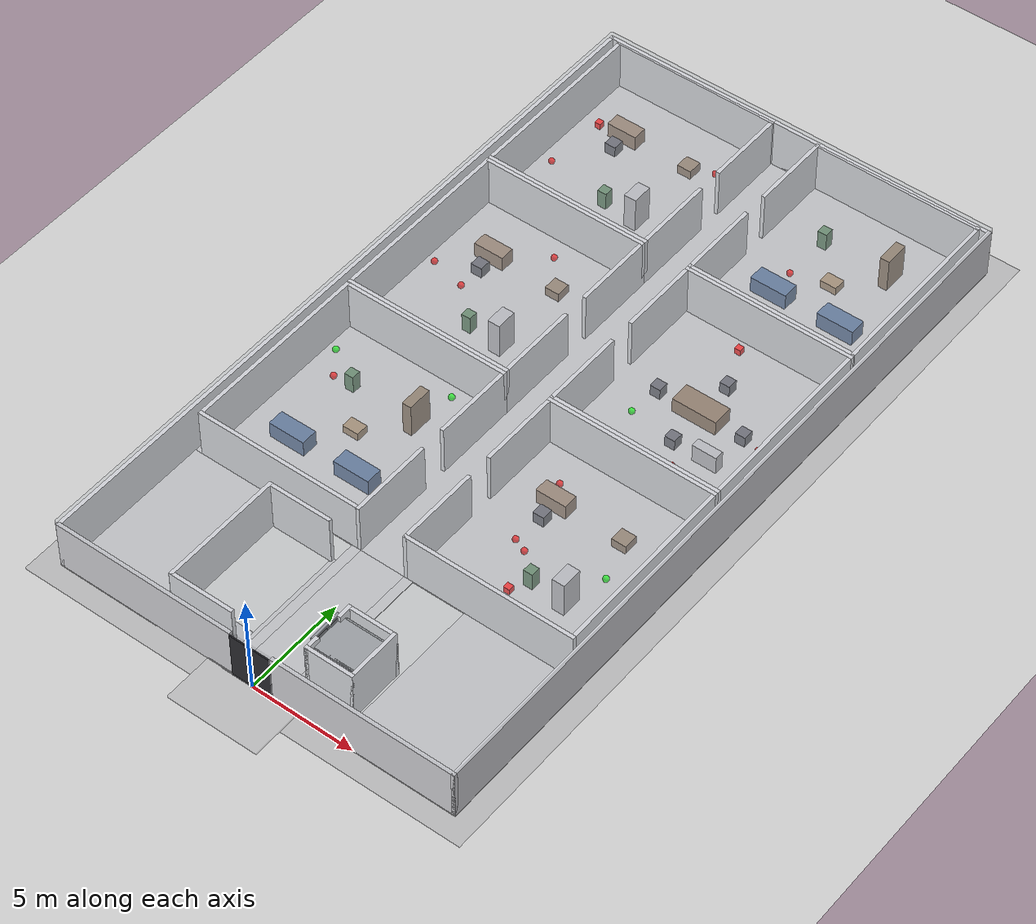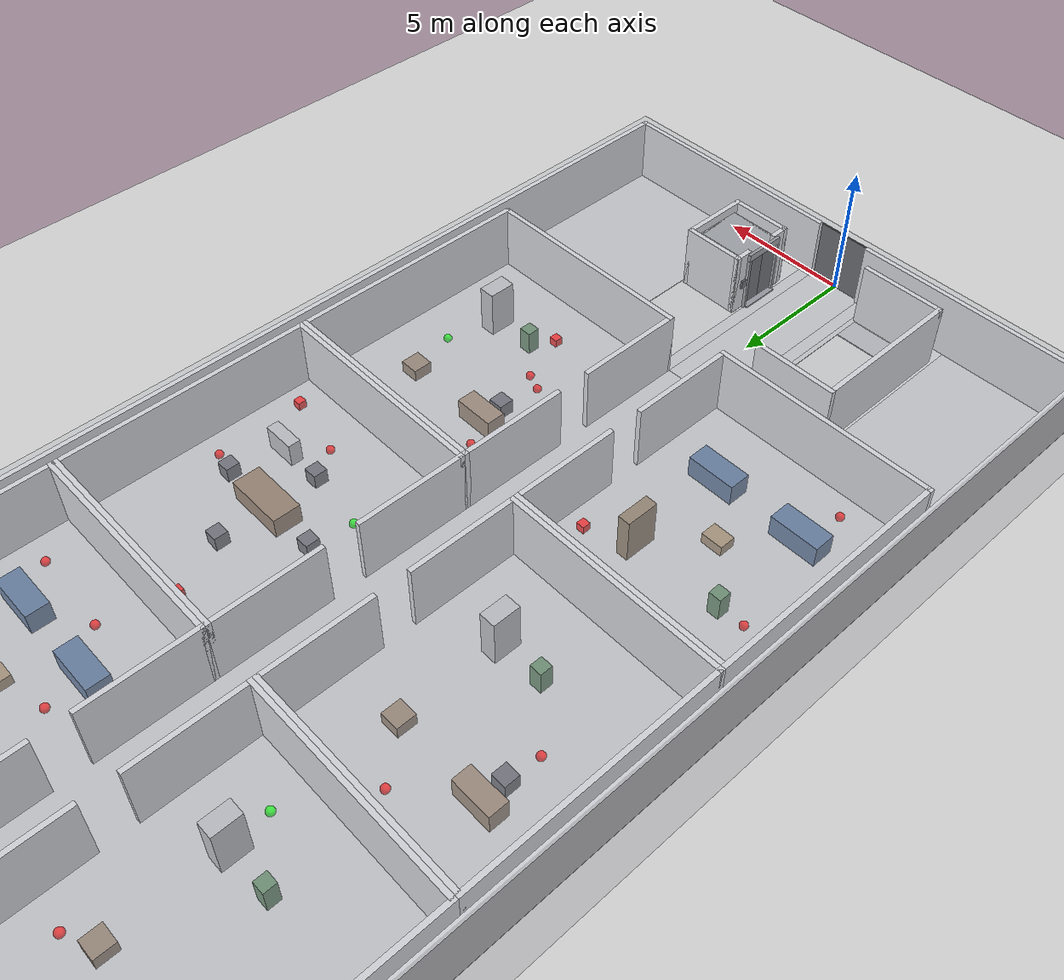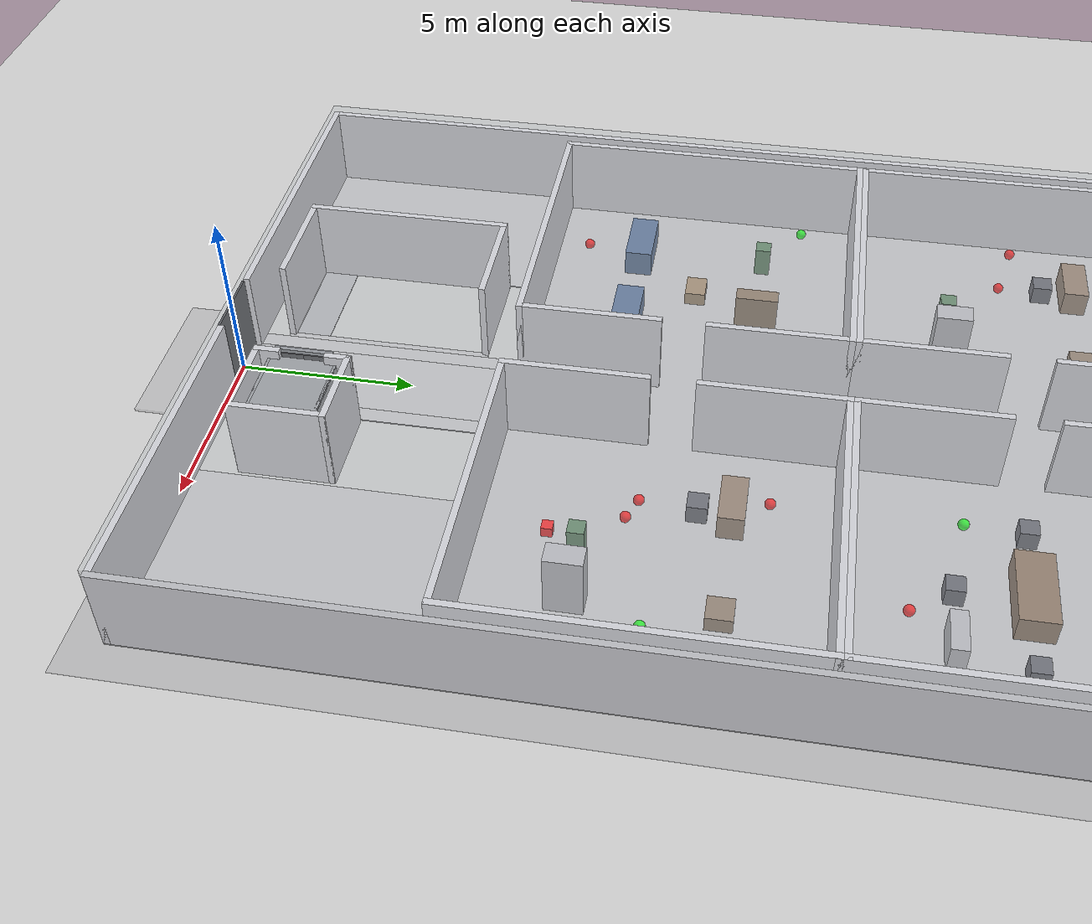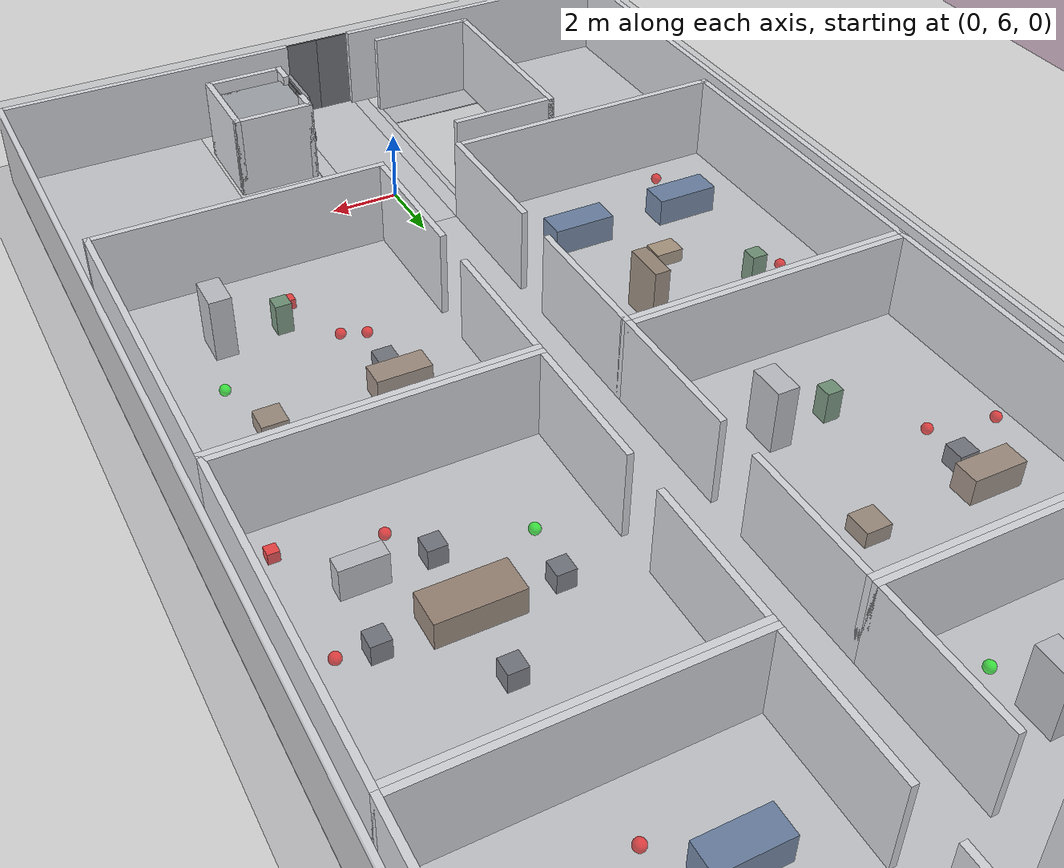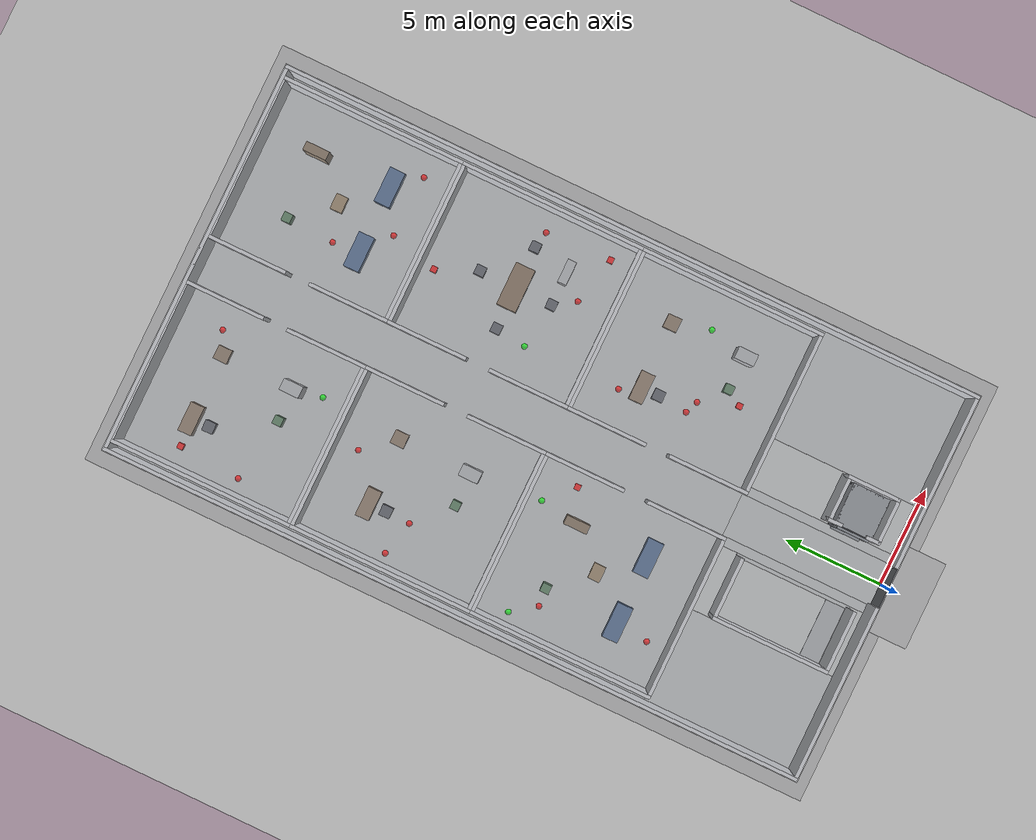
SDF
<?xml version="1.0" ?>
<sdf version="1.7">

  <world name="generated_world">

    <include>

      <uri>model://sun</uri>

    </include>

    <include>

      <uri>model://ground_plane</uri>

    </include>

    <model name="generated_building">

      <static>true</static>

      <pose>0 0 0 0 0 0</pose>

      <link name="foundation">

        <pose>0.0000 18.0000 -0.1500 0.0000 0.0000 0.0000</pose>

        <collision name="foundation_collision">

          <geometry>

            <box>

              <size>22.0000 38.0000 0.3000</size>

            </box>

          </geometry>

        </collision>

        <visual name="foundation_visual">

          <geometry>

            <box>

              <size>22.0000 38.0000 0.3000</size>

            </box>

          </geometry>

          <material>

            <ambient>0.58 0.58 0.60 0.35</ambient>

            <diffuse>0.58 0.58 0.60 0.35</diffuse>

          </material>

        </visual>

        <gravity>false</gravity>

      </link>

      <link name="entrance_apron">

        <pose>0.0000 -1.2000 0.0400 0.0000 0.0000 0.0000</pose>

        <collision name="entrance_apron_collision">

          <geometry>

            <box>

              <size>4.5000 2.4000 0.0800</size>

            </box>

          </geometry>

        </collision>

        <visual name="entrance_apron_visual">

          <geometry>

            <box>

              <size>4.5000 2.4000 0.0800</size>

            </box>

          </geometry>

          <material>

            <ambient>0.62 0.62 0.64 0.35</ambient>

            <diffuse>0.62 0.62 0.64 0.35</diffuse>

          </material>

        </visual>

        <gravity>false</gravity>

      </link>

      <link name="slab_floor_0_0">

        <pose>0.0000 21.9250 -0.1100 0.0000 0.0000 0.0000</pose>

        <collision name="slab_floor_0_0_collision">

          <geometry>

            <box>

              <size>20.0000 28.1500 0.2200</size>

            </box>

          </geometry>

        </collision>

        <visual name="slab_floor_0_0_visual">

          <geometry>

            <box>

              <size>20.0000 28.1500 0.2200</size>

            </box>

          </geometry>

          <material>

            <ambient>0.76 0.76 0.77 1.0</ambient>

            <diffuse>0.76 0.76 0.77 1.0</diffuse>

          </material>

        </visual>

        <gravity>false</gravity>

      </link>

      <link name="slab_floor_0_1">

        <pose>-7.4700 3.9250 -0.1100 0.0000 0.0000 0.0000</pose>

        <collision name="slab_floor_0_1_collision">

          <geometry>

            <box>

              <size>5.0600 7.8500 0.2200</size>

            </box>

          </geometry>

        </collision>

        <visual name="slab_floor_0_1_visual">

          <geometry>

            <box>

              <size>5.0600 7.8500 0.2200</size>

            </box>

          </geometry>

          <material>

            <ambient>0.76 0.76 0.77 1.0</ambient>

            <diffuse>0.76 0.76 0.77 1.0</diffuse>

          </material>

        </visual>

        <gravity>false</gravity>

      </link>

      <link name="slab_floor_0_2">

        <pose>-1.3300 3.9250 -0.1100 0.0000 0.0000 0.0000</pose>

        <collision name="slab_floor_0_2_collision">

          <geometry>

            <box>

              <size>0.4600 7.8500 0.2200</size>

            </box>

          </geometry>

        </collision>

        <visual name="slab_floor_0_2_visual">

          <geometry>

            <box>

              <size>0.4600 7.8500 0.2200</size>

            </box>

          </geometry>

          <material>

            <ambient>0.76 0.76 0.77 1.0</ambient>

            <diffuse>0.76 0.76 0.77 1.0</diffuse>

          </material>

        </visual>

        <gravity>false</gravity>

      </link>

      <link name="slab_floor_0_3">

        <pose>0.0000 3.9250 -0.1100 0.0000 0.0000 0.0000</pose>

        <collision name="slab_floor_0_3_collision">

          <geometry>

            <box>

              <size>2.2000 7.8500 0.2200</size>

            </box>

          </geometry>

        </collision>

        <visual name="slab_floor_0_3_visual">

          <geometry>

            <box>

              <size>2.2000 7.8500 0.2200</size>

            </box>

          </geometry>

          <material>

            <ambient>0.76 0.76 0.77 1.0</ambient>

            <diffuse>0.76 0.76 0.77 1.0</diffuse>

          </material>

        </visual>

        <gravity>false</gravity>

      </link>

      <link name="slab_floor_0_4">

        <pose>1.3300 3.9250 -0.1100 0.0000 0.0000 0.0000</pose>

        <collision name="slab_floor_0_4_collision">

          <geometry>

            <box>

              <size>0.4600 7.8500 0.2200</size>

            </box>

          </geometry>

        </collision>

        <visual name="slab_floor_0_4_visual">

          <geometry>

            <box>

              <size>0.4600 7.8500 0.2200</size>

            </box>

          </geometry>

          <material>

            <ambient>0.76 0.76 0.77 1.0</ambient>

            <diffuse>0.76 0.76 0.77 1.0</diffuse>

          </material>

        </visual>

        <gravity>false</gravity>

      </link>

      <link name="slab_floor_0_5">

        <pose>7.0700 3.9250 -0.1100 0.0000 0.0000 0.0000</pose>

        <collision name="slab_floor_0_5_collision">

          <geometry>

            <box>

              <size>5.8600 7.8500 0.2200</size>

            </box>

          </geometry>

        </collision>

        <visual name="slab_floor_0_5_visual">

          <geometry>

            <box>

              <size>5.8600 7.8500 0.2200</size>

            </box>

          </geometry>

          <material>

            <ambient>0.76 0.76 0.77 1.0</ambient>

            <diffuse>0.76 0.76 0.77 1.0</diffuse>

          </material>

        </visual>

        <gravity>false</gravity>

      </link>

      <link name="stair_edge_infill_floor_0">

        <pose>-1.6500 3.8500 -0.1100 0.0000 0.0000 0.0000</pose>

        <collision name="stair_edge_infill_floor_0_collision">

          <geometry>

            <box>

              <size>0.1800 6.0000 0.2200</size>

            </box>

          </geometry>

        </collision>

        <visual name="stair_edge_infill_floor_0_visual">

          <geometry>

            <box>

              <size>0.1800 6.0000 0.2200</size>

            </box>

          </geometry>

          <material>

            <ambient>0.76 0.76 0.77 1.0</ambient>

            <diffuse>0.76 0.76 0.77 1.0</diffuse>

          </material>

        </visual>

        <gravity>false</gravity>

      </link>

      <link name="exterior_west_floor_0">

        <pose>-9.9100 18.0000 1.2250 0.0000 0.0000 0.0000</pose>

        <collision name="exterior_west_floor_0_collision">

          <geometry>

            <box>

              <size>0.1800 36.0000 2.4500</size>

            </box>

          </geometry>

        </collision>

        <visual name="exterior_west_floor_0_visual">

          <geometry>

            <box>

              <size>0.1800 36.0000 2.4500</size>

            </box>

          </geometry>

          <material>

            <ambient>0.86 0.86 0.88 1</ambient>

            <diffuse>0.86 0.86 0.88 1</diffuse>

          </material>

        </visual>

        <gravity>false</gravity>

      </link>

      <link name="exterior_east_floor_0">

        <pose>9.9100 18.0000 1.2250 0.0000 0.0000 0.0000</pose>

        <collision name="exterior_east_floor_0_collision">

          <geometry>

            <box>

              <size>0.1800 36.0000 2.4500</size>

            </box>

          </geometry>

        </collision>

        <visual name="exterior_east_floor_0_visual">

          <geometry>

            <box>

              <size>0.1800 36.0000 2.4500</size>

            </box>

          </geometry>

          <material>

            <ambient>0.86 0.86 0.88 1</ambient>

            <diffuse>0.86 0.86 0.88 1</diffuse>

          </material>

        </visual>

        <gravity>false</gravity>

      </link>

      <link name="exterior_north_floor_0">

        <pose>0.0000 35.9100 1.2250 0.0000 0.0000 0.0000</pose>

        <collision name="exterior_north_floor_0_collision">

          <geometry>

            <box>

              <size>20.0000 0.1800 2.4500</size>

            </box>

          </geometry>

        </collision>

        <visual name="exterior_north_floor_0_visual">

          <geometry>

            <box>

              <size>20.0000 0.1800 2.4500</size>

            </box>

          </geometry>

          <material>

            <ambient>0.86 0.86 0.88 1</ambient>

            <diffuse>0.86 0.86 0.88 1</diffuse>

          </material>

        </visual>

        <gravity>false</gravity>

      </link>

      <link name="exterior_south_entrance_left">

        <pose>-5.5100 0.0900 1.2250 0.0000 0.0000 0.0000</pose>

        <collision name="exterior_south_entrance_left_collision">

          <geometry>

            <box>

              <size>8.9800 0.1800 2.4500</size>

            </box>

          </geometry>

        </collision>

        <visual name="exterior_south_entrance_left_visual">

          <geometry>

            <box>

              <size>8.9800 0.1800 2.4500</size>

            </box>

          </geometry>

          <material>

            <ambient>0.86 0.86 0.88 1</ambient>

            <diffuse>0.86 0.86 0.88 1</diffuse>

          </material>

        </visual>

        <gravity>false</gravity>

      </link>

      <link name="exterior_south_entrance_right">

        <pose>5.5100 0.0900 1.2250 0.0000 0.0000 0.0000</pose>

        <collision name="exterior_south_entrance_right_collision">

          <geometry>

            <box>

              <size>8.9800 0.1800 2.4500</size>

            </box>

          </geometry>

        </collision>

        <visual name="exterior_south_entrance_right_visual">

          <geometry>

            <box>

              <size>8.9800 0.1800 2.4500</size>

            </box>

          </geometry>

          <material>

            <ambient>0.86 0.86 0.88 1</ambient>

            <diffuse>0.86 0.86 0.88 1</diffuse>

          </material>

        </visual>

        <gravity>false</gravity>

      </link>

      <link name="north_end_wall_floor_0">

        <pose>0.0000 35.9100 1.2250 0.0000 0.0000 0.0000</pose>

        <collision name="north_end_wall_floor_0_collision">

          <geometry>

            <box>

              <size>2.2000 0.1800 2.4500</size>

            </box>

          </geometry>

        </collision>

        <visual name="north_end_wall_floor_0_visual">

          <geometry>

            <box>

              <size>2.2000 0.1800 2.4500</size>

            </box>

          </geometry>

          <material>

            <ambient>0.86 0.86 0.88 1</ambient>

            <diffuse>0.86 0.86 0.88 1</diffuse>

          </material>

        </visual>

        <gravity>false</gravity>

      </link>

      <link name="floor_0_room_0_corridor_wall_lower">

        <pose>-1.1900 9.8883 1.2250 0.0000 0.0000 0.0000</pose>

        <collision name="floor_0_room_0_corridor_wall_lower_collision">

          <geometry>

            <box>

              <size>0.1800 4.0767 2.4500</size>

            </box>

          </geometry>

        </collision>

        <visual name="floor_0_room_0_corridor_wall_lower_visual">

          <geometry>

            <box>

              <size>0.1800 4.0767 2.4500</size>

            </box>

          </geometry>

          <material>

            <ambient>0.86 0.86 0.88 1</ambient>

            <diffuse>0.86 0.86 0.88 1</diffuse>

          </material>

        </visual>

        <gravity>false</gravity>

      </link>

      <link name="floor_0_room_0_corridor_wall_upper">

        <pose>-1.1900 15.1650 1.2250 0.0000 0.0000 0.0000</pose>

        <collision name="floor_0_room_0_corridor_wall_upper_collision">

          <geometry>

            <box>

              <size>0.1800 4.0767 2.4500</size>

            </box>

          </geometry>

        </collision>

        <visual name="floor_0_room_0_corridor_wall_upper_visual">

          <geometry>

            <box>

              <size>0.1800 4.0767 2.4500</size>

            </box>

          </geometry>

          <material>

            <ambient>0.86 0.86 0.88 1</ambient>

            <diffuse>0.86 0.86 0.88 1</diffuse>

          </material>

        </visual>

        <gravity>false</gravity>

      </link>

      <link name="floor_0_room_0_west_wall">

        <pose>-9.4100 12.5267 1.2250 0.0000 0.0000 0.0000</pose>

        <collision name="floor_0_room_0_west_wall_collision">

          <geometry>

            <box>

              <size>0.1800 9.3533 2.4500</size>

            </box>

          </geometry>

        </collision>

        <visual name="floor_0_room_0_west_wall_visual">

          <geometry>

            <box>

              <size>0.1800 9.3533 2.4500</size>

            </box>

          </geometry>

          <material>

            <ambient>0.86 0.86 0.88 1</ambient>

            <diffuse>0.86 0.86 0.88 1</diffuse>

          </material>

        </visual>

        <gravity>false</gravity>

      </link>

      <link name="floor_0_room_0_south_wall">

        <pose>-5.3000 7.9400 1.2250 0.0000 0.0000 0.0000</pose>

        <collision name="floor_0_room_0_south_wall_collision">

          <geometry>

            <box>

              <size>8.4000 0.1800 2.4500</size>

            </box>

          </geometry>

        </collision>

        <visual name="floor_0_room_0_south_wall_visual">

          <geometry>

            <box>

              <size>8.4000 0.1800 2.4500</size>

            </box>

          </geometry>

          <material>

            <ambient>0.86 0.86 0.88 1</ambient>

            <diffuse>0.86 0.86 0.88 1</diffuse>

          </material>

        </visual>

        <gravity>false</gravity>

      </link>

      <link name="floor_0_room_0_north_wall">

        <pose>-5.3000 17.1133 1.2250 0.0000 0.0000 0.0000</pose>

        <collision name="floor_0_room_0_north_wall_collision">

          <geometry>

            <box>

              <size>8.4000 0.1800 2.4500</size>

            </box>

          </geometry>

        </collision>

        <visual name="floor_0_room_0_north_wall_visual">

          <geometry>

            <box>

              <size>8.4000 0.1800 2.4500</size>

            </box>

          </geometry>

          <material>

            <ambient>0.86 0.86 0.88 1</ambient>

            <diffuse>0.86 0.86 0.88 1</diffuse>

          </material>

        </visual>

        <gravity>false</gravity>

      </link>

      <link name="floor_0_room_1_corridor_wall_lower">

        <pose>1.1900 9.8883 1.2250 0.0000 0.0000 0.0000</pose>

        <collision name="floor_0_room_1_corridor_wall_lower_collision">

          <geometry>

            <box>

              <size>0.1800 4.0767 2.4500</size>

            </box>

          </geometry>

        </collision>

        <visual name="floor_0_room_1_corridor_wall_lower_visual">

          <geometry>

            <box>

              <size>0.1800 4.0767 2.4500</size>

            </box>

          </geometry>

          <material>

            <ambient>0.86 0.86 0.88 1</ambient>

            <diffuse>0.86 0.86 0.88 1</diffuse>

          </material>

        </visual>

        <gravity>false</gravity>

      </link>

      <link name="floor_0_room_1_corridor_wall_upper">

        <pose>1.1900 15.1650 1.2250 0.0000 0.0000 0.0000</pose>

        <collision name="floor_0_room_1_corridor_wall_upper_collision">

          <geometry>

            <box>

              <size>0.1800 4.0767 2.4500</size>

            </box>

          </geometry>

        </collision>

        <visual name="floor_0_room_1_corridor_wall_upper_visual">

          <geometry>

            <box>

              <size>0.1800 4.0767 2.4500</size>

            </box>

          </geometry>

          <material>

            <ambient>0.86 0.86 0.88 1</ambient>

            <diffuse>0.86 0.86 0.88 1</diffuse>

          </material>

        </visual>

        <gravity>false</gravity>

      </link>

      <link name="floor_0_room_1_east_wall">

        <pose>9.4100 12.5267 1.2250 0.0000 0.0000 0.0000</pose>

        <collision name="floor_0_room_1_east_wall_collision">

          <geometry>

            <box>

              <size>0.1800 9.3533 2.4500</size>

            </box>

          </geometry>

        </collision>

        <visual name="floor_0_room_1_east_wall_visual">

          <geometry>

            <box>

              <size>0.1800 9.3533 2.4500</size>

            </box>

          </geometry>

          <material>

            <ambient>0.86 0.86 0.88 1</ambient>

            <diffuse>0.86 0.86 0.88 1</diffuse>

          </material>

        </visual>

        <gravity>false</gravity>

      </link>

      <link name="floor_0_room_1_south_wall">

        <pose>5.3000 7.9400 1.2250 0.0000 0.0000 0.0000</pose>

        <collision name="floor_0_room_1_south_wall_collision">

          <geometry>

            <box>

              <size>8.4000 0.1800 2.4500</size>

            </box>

          </geometry>

        </collision>

        <visual name="floor_0_room_1_south_wall_visual">

          <geometry>

            <box>

              <size>8.4000 0.1800 2.4500</size>

            </box>

          </geometry>

          <material>

            <ambient>0.86 0.86 0.88 1</ambient>

            <diffuse>0.86 0.86 0.88 1</diffuse>

          </material>

        </visual>

        <gravity>false</gravity>

      </link>

      <link name="floor_0_room_1_north_wall">

        <pose>5.3000 17.1133 1.2250 0.0000 0.0000 0.0000</pose>

        <collision name="floor_0_room_1_north_wall_collision">

          <geometry>

            <box>

              <size>8.4000 0.1800 2.4500</size>

            </box>

          </geometry>

        </collision>

        <visual name="floor_0_room_1_north_wall_visual">

          <geometry>

            <box>

              <size>8.4000 0.1800 2.4500</size>

            </box>

          </geometry>

          <material>

            <ambient>0.86 0.86 0.88 1</ambient>

            <diffuse>0.86 0.86 0.88 1</diffuse>

          </material>

        </visual>

        <gravity>false</gravity>

      </link>

      <link name="floor_0_room_2_corridor_wall_lower">

        <pose>-1.1900 19.2417 1.2250 0.0000 0.0000 0.0000</pose>

        <collision name="floor_0_room_2_corridor_wall_lower_collision">

          <geometry>

            <box>

              <size>0.1800 4.0767 2.4500</size>

            </box>

          </geometry>

        </collision>

        <visual name="floor_0_room_2_corridor_wall_lower_visual">

          <geometry>

            <box>

              <size>0.1800 4.0767 2.4500</size>

            </box>

          </geometry>

          <material>

            <ambient>0.86 0.86 0.88 1</ambient>

            <diffuse>0.86 0.86 0.88 1</diffuse>

          </material>

        </visual>

        <gravity>false</gravity>

      </link>

      <link name="floor_0_room_2_corridor_wall_upper">

        <pose>-1.1900 24.5183 1.2250 0.0000 0.0000 0.0000</pose>

        <collision name="floor_0_room_2_corridor_wall_upper_collision">

          <geometry>

            <box>

              <size>0.1800 4.0767 2.4500</size>

            </box>

          </geometry>

        </collision>

        <visual name="floor_0_room_2_corridor_wall_upper_visual">

          <geometry>

            <box>

              <size>0.1800 4.0767 2.4500</size>

            </box>

          </geometry>

          <material>

            <ambient>0.86 0.86 0.88 1</ambient>

            <diffuse>0.86 0.86 0.88 1</diffuse>

          </material>

        </visual>

        <gravity>false</gravity>

      </link>

      <link name="floor_0_room_2_west_wall">

        <pose>-9.4100 21.8800 1.2250 0.0000 0.0000 0.0000</pose>

        <collision name="floor_0_room_2_west_wall_collision">

          <geometry>

            <box>

              <size>0.1800 9.3533 2.4500</size>

            </box>

          </geometry>

        </collision>

        <visual name="floor_0_room_2_west_wall_visual">

          <geometry>

            <box>

              <size>0.1800 9.3533 2.4500</size>

            </box>

          </geometry>

          <material>

            <ambient>0.86 0.86 0.88 1</ambient>

            <diffuse>0.86 0.86 0.88 1</diffuse>

          </material>

        </visual>

        <gravity>false</gravity>

      </link>

      <link name="floor_0_room_2_south_wall">

        <pose>-5.3000 17.2933 1.2250 0.0000 0.0000 0.0000</pose>

        <collision name="floor_0_room_2_south_wall_collision">

          <geometry>

            <box>

              <size>8.4000 0.1800 2.4500</size>

            </box>

          </geometry>

        </collision>

        <visual name="floor_0_room_2_south_wall_visual">

          <geometry>

            <box>

              <size>8.4000 0.1800 2.4500</size>

            </box>

          </geometry>

          <material>

            <ambient>0.86 0.86 0.88 1</ambient>

            <diffuse>0.86 0.86 0.88 1</diffuse>

          </material>

        </visual>

        <gravity>false</gravity>

      </link>

      <link name="floor_0_room_2_north_wall">

        <pose>-5.3000 26.4667 1.2250 0.0000 0.0000 0.0000</pose>

        <collision name="floor_0_room_2_north_wall_collision">

          <geometry>

            <box>

              <size>8.4000 0.1800 2.4500</size>

            </box>

          </geometry>

        </collision>

        <visual name="floor_0_room_2_north_wall_visual">

          <geometry>

            <box>

              <size>8.4000 0.1800 2.4500</size>

            </box>

          </geometry>

          <material>

            <ambient>0.86 0.86 0.88 1</ambient>

            <diffuse>0.86 0.86 0.88 1</diffuse>

          </material>

        </visual>

        <gravity>false</gravity>

      </link>

      <link name="floor_0_room_3_corridor_wall_lower">

        <pose>1.1900 19.2417 1.2250 0.0000 0.0000 0.0000</pose>

        <collision name="floor_0_room_3_corridor_wall_lower_collision">

          <geometry>

            <box>

              <size>0.1800 4.0767 2.4500</size>

            </box>

          </geometry>

        </collision>

        <visual name="floor_0_room_3_corridor_wall_lower_visual">

          <geometry>

            <box>

              <size>0.1800 4.0767 2.4500</size>

            </box>

          </geometry>

          <material>

            <ambient>0.86 0.86 0.88 1</ambient>

            <diffuse>0.86 0.86 0.88 1</diffuse>

          </material>

        </visual>

        <gravity>false</gravity>

      </link>

      <link name="floor_0_room_3_corridor_wall_upper">

        <pose>1.1900 24.5183 1.2250 0.0000 0.0000 0.0000</pose>

        <collision name="floor_0_room_3_corridor_wall_upper_collision">

          <geometry>

            <box>

              <size>0.1800 4.0767 2.4500</size>

            </box>

          </geometry>

        </collision>

        <visual name="floor_0_room_3_corridor_wall_upper_visual">

          <geometry>

            <box>

              <size>0.1800 4.0767 2.4500</size>

            </box>

          </geometry>

          <material>

            <ambient>0.86 0.86 0.88 1</ambient>

            <diffuse>0.86 0.86 0.88 1</diffuse>

          </material>

        </visual>

        <gravity>false</gravity>

      </link>

      <link name="floor_0_room_3_east_wall">

        <pose>9.4100 21.8800 1.2250 0.0000 0.0000 0.0000</pose>

        <collision name="floor_0_room_3_east_wall_collision">

          <geometry>

            <box>

              <size>0.1800 9.3533 2.4500</size>

            </box>

          </geometry>

        </collision>

        <visual name="floor_0_room_3_east_wall_visual">

          <geometry>

            <box>

              <size>0.1800 9.3533 2.4500</size>

            </box>

          </geometry>

          <material>

            <ambient>0.86 0.86 0.88 1</ambient>

            <diffuse>0.86 0.86 0.88 1</diffuse>

          </material>

        </visual>

        <gravity>false</gravity>

      </link>

      <link name="floor_0_room_3_south_wall">

        <pose>5.3000 17.2933 1.2250 0.0000 0.0000 0.0000</pose>

        <collision name="floor_0_room_3_south_wall_collision">

          <geometry>

            <box>

              <size>8.4000 0.1800 2.4500</size>

            </box>

          </geometry>

        </collision>

        <visual name="floor_0_room_3_south_wall_visual">

          <geometry>

            <box>

              <size>8.4000 0.1800 2.4500</size>

            </box>

          </geometry>

          <material>

            <ambient>0.86 0.86 0.88 1</ambient>

            <diffuse>0.86 0.86 0.88 1</diffuse>

          </material>

        </visual>

        <gravity>false</gravity>

      </link>

      <link name="floor_0_room_3_north_wall">

        <pose>5.3000 26.4667 1.2250 0.0000 0.0000 0.0000</pose>

        <collision name="floor_0_room_3_north_wall_collision">

          <geometry>

            <box>

              <size>8.4000 0.1800 2.4500</size>

            </box>

          </geometry>

        </collision>

        <visual name="floor_0_room_3_north_wall_visual">

          <geometry>

            <box>

              <size>8.4000 0.1800 2.4500</size>

            </box>

          </geometry>

          <material>

            <ambient>0.86 0.86 0.88 1</ambient>

            <diffuse>0.86 0.86 0.88 1</diffuse>

          </material>

        </visual>

        <gravity>false</gravity>

      </link>

      <link name="floor_0_room_4_corridor_wall_lower">

        <pose>-1.1900 28.5950 1.2250 0.0000 0.0000 0.0000</pose>

        <collision name="floor_0_room_4_corridor_wall_lower_collision">

          <geometry>

            <box>

              <size>0.1800 4.0767 2.4500</size>

            </box>

          </geometry>

        </collision>

        <visual name="floor_0_room_4_corridor_wall_lower_visual">

          <geometry>

            <box>

              <size>0.1800 4.0767 2.4500</size>

            </box>

          </geometry>

          <material>

            <ambient>0.86 0.86 0.88 1</ambient>

            <diffuse>0.86 0.86 0.88 1</diffuse>

          </material>

        </visual>

        <gravity>false</gravity>

      </link>

      <link name="floor_0_room_4_corridor_wall_upper">

        <pose>-1.1900 33.8717 1.2250 0.0000 0.0000 0.0000</pose>

        <collision name="floor_0_room_4_corridor_wall_upper_collision">

          <geometry>

            <box>

              <size>0.1800 4.0767 2.4500</size>

            </box>

          </geometry>

        </collision>

        <visual name="floor_0_room_4_corridor_wall_upper_visual">

          <geometry>

            <box>

              <size>0.1800 4.0767 2.4500</size>

            </box>

          </geometry>

          <material>

            <ambient>0.86 0.86 0.88 1</ambient>

            <diffuse>0.86 0.86 0.88 1</diffuse>

          </material>

        </visual>

        <gravity>false</gravity>

      </link>

      <link name="floor_0_room_4_west_wall">

        <pose>-9.4100 31.2333 1.2250 0.0000 0.0000 0.0000</pose>

        <collision name="floor_0_room_4_west_wall_collision">

          <geometry>

            <box>

              <size>0.1800 9.3533 2.4500</size>

            </box>

          </geometry>

        </collision>

        <visual name="floor_0_room_4_west_wall_visual">

          <geometry>

            <box>

              <size>0.1800 9.3533 2.4500</size>

            </box>

          </geometry>

          <material>

            <ambient>0.86 0.86 0.88 1</ambient>

            <diffuse>0.86 0.86 0.88 1</diffuse>

          </material>

        </visual>

        <gravity>false</gravity>

      </link>

      <link name="floor_0_room_4_south_wall">

        <pose>-5.3000 26.6467 1.2250 0.0000 0.0000 0.0000</pose>

        <collision name="floor_0_room_4_south_wall_collision">

          <geometry>

            <box>

              <size>8.4000 0.1800 2.4500</size>

            </box>

          </geometry>

        </collision>

        <visual name="floor_0_room_4_south_wall_visual">

          <geometry>

            <box>

              <size>8.4000 0.1800 2.4500</size>

            </box>

          </geometry>

          <material>

            <ambient>0.86 0.86 0.88 1</ambient>

            <diffuse>0.86 0.86 0.88 1</diffuse>

          </material>

        </visual>

        <gravity>false</gravity>

      </link>

      <link name="floor_0_room_4_north_wall">

        <pose>-5.3000 35.8200 1.2250 0.0000 0.0000 0.0000</pose>

        <collision name="floor_0_room_4_north_wall_collision">

          <geometry>

            <box>

              <size>8.4000 0.1800 2.4500</size>

            </box>

          </geometry>

        </collision>

        <visual name="floor_0_room_4_north_wall_visual">

          <geometry>

            <box>

              <size>8.4000 0.1800 2.4500</size>

            </box>

          </geometry>

          <material>

            <ambient>0.86 0.86 0.88 1</ambient>

            <diffuse>0.86 0.86 0.88 1</diffuse>

          </material>

        </visual>

        <gravity>false</gravity>

      </link>

      <link name="floor_0_room_5_corridor_wall_lower">

        <pose>1.1900 28.5950 1.2250 0.0000 0.0000 0.0000</pose>

        <collision name="floor_0_room_5_corridor_wall_lower_collision">

          <geometry>

            <box>

              <size>0.1800 4.0767 2.4500</size>

            </box>

          </geometry>

        </collision>

        <visual name="floor_0_room_5_corridor_wall_lower_visual">

          <geometry>

            <box>

              <size>0.1800 4.0767 2.4500</size>

            </box>

          </geometry>

          <material>

            <ambient>0.86 0.86 0.88 1</ambient>

            <diffuse>0.86 0.86 0.88 1</diffuse>

          </material>

        </visual>

        <gravity>false</gravity>

      </link>

      <link name="floor_0_room_5_corridor_wall_upper">

        <pose>1.1900 33.8717 1.2250 0.0000 0.0000 0.0000</pose>

        <collision name="floor_0_room_5_corridor_wall_upper_collision">

          <geometry>

            <box>

              <size>0.1800 4.0767 2.4500</size>

            </box>

          </geometry>

        </collision>

        <visual name="floor_0_room_5_corridor_wall_upper_visual">

          <geometry>

            <box>

              <size>0.1800 4.0767 2.4500</size>

            </box>

          </geometry>

          <material>

            <ambient>0.86 0.86 0.88 1</ambient>

            <diffuse>0.86 0.86 0.88 1</diffuse>

          </material>

        </visual>

        <gravity>false</gravity>

      </link>

      <link name="floor_0_room_5_east_wall">

        <pose>9.4100 31.2333 1.2250 0.0000 0.0000 0.0000</pose>

        <collision name="floor_0_room_5_east_wall_collision">

          <geometry>

            <box>

              <size>0.1800 9.3533 2.4500</size>

            </box>

          </geometry>

        </collision>

        <visual name="floor_0_room_5_east_wall_visual">

          <geometry>

            <box>

              <size>0.1800 9.3533 2.4500</size>

            </box>

          </geometry>

          <material>

            <ambient>0.86 0.86 0.88 1</ambient>

            <diffuse>0.86 0.86 0.88 1</diffuse>

          </material>

        </visual>

        <gravity>false</gravity>

      </link>

      <link name="floor_0_room_5_south_wall">

        <pose>5.3000 26.6467 1.2250 0.0000 0.0000 0.0000</pose>

        <collision name="floor_0_room_5_south_wall_collision">

          <geometry>

            <box>

              <size>8.4000 0.1800 2.4500</size>

            </box>

          </geometry>

        </collision>

        <visual name="floor_0_room_5_south_wall_visual">

          <geometry>

            <box>

              <size>8.4000 0.1800 2.4500</size>

            </box>

          </geometry>

          <material>

            <ambient>0.86 0.86 0.88 1</ambient>

            <diffuse>0.86 0.86 0.88 1</diffuse>

          </material>

        </visual>

        <gravity>false</gravity>

      </link>

      <link name="floor_0_room_5_north_wall">

        <pose>5.3000 35.8200 1.2250 0.0000 0.0000 0.0000</pose>

        <collision name="floor_0_room_5_north_wall_collision">

          <geometry>

            <box>

              <size>8.4000 0.1800 2.4500</size>

            </box>

          </geometry>

        </collision>

        <visual name="floor_0_room_5_north_wall_visual">

          <geometry>

            <box>

              <size>8.4000 0.1800 2.4500</size>

            </box>

          </geometry>

          <material>

            <ambient>0.86 0.86 0.88 1</ambient>

            <diffuse>0.86 0.86 0.88 1</diffuse>

          </material>

        </visual>

        <gravity>false</gravity>

      </link>

      <link name="stair_core_floor_0_west">

        <pose>-4.7600 3.8500 1.2250 0.0000 0.0000 0.0000</pose>

        <collision name="stair_core_floor_0_west_collision">

          <geometry>

            <box>

              <size>0.1800 6.0000 2.4500</size>

            </box>

          </geometry>

        </collision>

        <visual name="stair_core_floor_0_west_visual">

          <geometry>

            <box>

              <size>0.1800 6.0000 2.4500</size>

            </box>

          </geometry>

          <material>

            <ambient>0.86 0.86 0.88 1</ambient>

            <diffuse>0.86 0.86 0.88 1</diffuse>

          </material>

        </visual>

        <gravity>false</gravity>

      </link>

      <link name="stair_core_floor_0_south">

        <pose>-3.2500 0.9400 1.2250 0.0000 0.0000 0.0000</pose>

        <collision name="stair_core_floor_0_south_collision">

          <geometry>

            <box>

              <size>3.2000 0.1800 2.4500</size>

            </box>

          </geometry>

        </collision>

        <visual name="stair_core_floor_0_south_visual">

          <geometry>

            <box>

              <size>3.2000 0.1800 2.4500</size>

            </box>

          </geometry>

          <material>

            <ambient>0.86 0.86 0.88 1</ambient>

            <diffuse>0.86 0.86 0.88 1</diffuse>

          </material>

        </visual>

        <gravity>false</gravity>

      </link>

      <link name="stair_core_floor_0_north">

        <pose>-3.2500 6.7600 1.2250 0.0000 0.0000 0.0000</pose>

        <collision name="stair_core_floor_0_north_collision">

          <geometry>

            <box>

              <size>3.2000 0.1800 2.4500</size>

            </box>

          </geometry>

        </collision>

        <visual name="stair_core_floor_0_north_visual">

          <geometry>

            <box>

              <size>3.2000 0.1800 2.4500</size>

            </box>

          </geometry>

          <material>

            <ambient>0.86 0.86 0.88 1</ambient>

            <diffuse>0.86 0.86 0.88 1</diffuse>

          </material>

        </visual>

        <gravity>false</gravity>

      </link>

      <link name="elevator_core_floor_0_west_lower">

        <pose>1.7400 1.6150 1.2250 0.0000 0.0000 0.0000</pose>

        <collision name="elevator_core_floor_0_west_lower_collision">

          <geometry>

            <box>

              <size>0.1800 0.7300 2.4500</size>

            </box>

          </geometry>

        </collision>

        <visual name="elevator_core_floor_0_west_lower_visual">

          <geometry>

            <box>

              <size>0.1800 0.7300 2.4500</size>

            </box>

          </geometry>

          <material>

            <ambient>0.86 0.86 0.88 1</ambient>

            <diffuse>0.86 0.86 0.88 1</diffuse>

          </material>

        </visual>

        <gravity>false</gravity>

      </link>

      <link name="elevator_core_floor_0_west_upper">

        <pose>1.7400 3.5850 1.2250 0.0000 0.0000 0.0000</pose>

        <collision name="elevator_core_floor_0_west_upper_collision">

          <geometry>

            <box>

              <size>0.1800 0.7300 2.4500</size>

            </box>

          </geometry>

        </collision>

        <visual name="elevator_core_floor_0_west_upper_visual">

          <geometry>

            <box>

              <size>0.1800 0.7300 2.4500</size>

            </box>

          </geometry>

          <material>

            <ambient>0.86 0.86 0.88 1</ambient>

            <diffuse>0.86 0.86 0.88 1</diffuse>

          </material>

        </visual>

        <gravity>false</gravity>

      </link>

      <link name="elevator_core_floor_0_east">

        <pose>3.9600 2.6000 1.2250 0.0000 0.0000 0.0000</pose>

        <collision name="elevator_core_floor_0_east_collision">

          <geometry>

            <box>

              <size>0.1800 2.7000 2.4500</size>

            </box>

          </geometry>

        </collision>

        <visual name="elevator_core_floor_0_east_visual">

          <geometry>

            <box>

              <size>0.1800 2.7000 2.4500</size>

            </box>

          </geometry>

          <material>

            <ambient>0.86 0.86 0.88 1</ambient>

            <diffuse>0.86 0.86 0.88 1</diffuse>

          </material>

        </visual>

        <gravity>false</gravity>

      </link>

      <link name="elevator_core_floor_0_south">

        <pose>2.8500 1.3400 1.2250 0.0000 0.0000 0.0000</pose>

        <collision name="elevator_core_floor_0_south_collision">

          <geometry>

            <box>

              <size>2.4000 0.1800 2.4500</size>

            </box>

          </geometry>

        </collision>

        <visual name="elevator_core_floor_0_south_visual">

          <geometry>

            <box>

              <size>2.4000 0.1800 2.4500</size>

            </box>

          </geometry>

          <material>

            <ambient>0.86 0.86 0.88 1</ambient>

            <diffuse>0.86 0.86 0.88 1</diffuse>

          </material>

        </visual>

        <gravity>false</gravity>

      </link>

      <link name="elevator_core_floor_0_north">

        <pose>2.8500 3.8600 1.2250 0.0000 0.0000 0.0000</pose>

        <collision name="elevator_core_floor_0_north_collision">

          <geometry>

            <box>

              <size>2.4000 0.1800 2.4500</size>

            </box>

          </geometry>

        </collision>

        <visual name="elevator_core_floor_0_north_visual">

          <geometry>

            <box>

              <size>2.4000 0.1800 2.4500</size>

            </box>

          </geometry>

          <material>

            <ambient>0.86 0.86 0.88 1</ambient>

            <diffuse>0.86 0.86 0.88 1</diffuse>

          </material>

        </visual>

        <gravity>false</gravity>

      </link>

      <link name="elevator_threshold_floor_0">

        <pose>1.5400 2.6000 0.0300 0.0000 0.0000 0.0000</pose>

        <collision name="elevator_threshold_floor_0_collision">

          <geometry>

            <box>

              <size>0.2200 1.5000 0.0600</size>

            </box>

          </geometry>

        </collision>

        <visual name="elevator_threshold_floor_0_visual">

          <geometry>

            <box>

              <size>0.2200 1.5000 0.0600</size>

            </box>

          </geometry>

          <material>

            <ambient>0.50 0.51 0.54 1</ambient>

            <diffuse>0.50 0.51 0.54 1</diffuse>

          </material>

        </visual>

        <gravity>false</gravity>

      </link>

      <link name="elevator_sill_infill_floor_0">

        <pose>1.6750 2.6000 -0.1100 0.0000 0.0000 0.0000</pose>

        <collision name="elevator_sill_infill_floor_0_collision">

          <geometry>

            <box>

              <size>0.0500 2.5200 0.2200</size>

            </box>

          </geometry>

        </collision>

        <visual name="elevator_sill_infill_floor_0_visual">

          <geometry>

            <box>

              <size>0.0500 2.5200 0.2200</size>

            </box>

          </geometry>

          <material>

            <ambient>0.72 0.72 0.73 1</ambient>

            <diffuse>0.72 0.72 0.73 1</diffuse>

          </material>

        </visual>

        <gravity>false</gravity>

      </link>

      <link name="elevator_header_floor_0">

        <pose>1.5900 2.6000 2.2600 0.0000 0.0000 0.0000</pose>

        <collision name="elevator_header_floor_0_collision">

          <geometry>

            <box>

              <size>0.1200 1.6000 0.2800</size>

            </box>

          </geometry>

        </collision>

        <visual name="elevator_header_floor_0_visual">

          <geometry>

            <box>

              <size>0.1200 1.6000 0.2800</size>

            </box>

          </geometry>

          <material>

            <ambient>0.50 0.51 0.54 1</ambient>

            <diffuse>0.50 0.51 0.54 1</diffuse>

          </material>

        </visual>

        <gravity>false</gravity>

      </link>

      <link name="elevator_jamb_left_floor_0">

        <pose>1.5900 1.8500 1.1000 0.0000 0.0000 0.0000</pose>

        <collision name="elevator_jamb_left_floor_0_collision">

          <geometry>

            <box>

              <size>0.1200 0.1000 2.2000</size>

            </box>

          </geometry>

        </collision>

        <visual name="elevator_jamb_left_floor_0_visual">

          <geometry>

            <box>

              <size>0.1200 0.1000 2.2000</size>

            </box>

          </geometry>

          <material>

            <ambient>0.50 0.51 0.54 1</ambient>

            <diffuse>0.50 0.51 0.54 1</diffuse>

          </material>

        </visual>

        <gravity>false</gravity>

      </link>

      <link name="elevator_jamb_right_floor_0">

        <pose>1.5900 3.3500 1.1000 0.0000 0.0000 0.0000</pose>

        <collision name="elevator_jamb_right_floor_0_collision">

          <geometry>

            <box>

              <size>0.1200 0.1000 2.2000</size>

            </box>

          </geometry>

        </collision>

        <visual name="elevator_jamb_right_floor_0_visual">

          <geometry>

            <box>

              <size>0.1200 0.1000 2.2000</size>

            </box>

          </geometry>

          <material>

            <ambient>0.50 0.51 0.54 1</ambient>

            <diffuse>0.50 0.51 0.54 1</diffuse>

          </material>

        </visual>

        <gravity>false</gravity>

      </link>

      <link name="elevator_call_panel_floor_0">

        <pose>1.5700 3.5800 1.2000 0.0000 0.0000 0.0000</pose>

        <collision name="elevator_call_panel_floor_0_collision">

          <geometry>

            <box>

              <size>0.0800 0.2200 0.3200</size>

            </box>

          </geometry>

        </collision>

        <visual name="elevator_call_panel_floor_0_visual">

          <geometry>

            <box>

              <size>0.0800 0.2200 0.3200</size>

            </box>

          </geometry>

          <material>

            <ambient>0.20 0.20 0.24 1</ambient>

            <diffuse>0.20 0.20 0.24 1</diffuse>

          </material>

        </visual>

        <gravity>false</gravity>

      </link>

      <link name="floor_0_room_0_sofa_a">

        <pose>-7.0000 10.6383 0.4500 0.0000 0.0000 0.0000</pose>

        <collision name="floor_0_room_0_sofa_a_collision">

          <geometry>

            <box>

              <size>1.8000 0.8000 0.8000</size>

            </box>

          </geometry>

        </collision>

        <visual name="floor_0_room_0_sofa_a_visual">

          <geometry>

            <box>

              <size>1.8000 0.8000 0.8000</size>

            </box>

          </geometry>

          <material>

            <ambient>0.24 0.36 0.54 1</ambient>

            <diffuse>0.24 0.36 0.54 1</diffuse>

          </material>

        </visual>

        <gravity>false</gravity>

      </link>

      <link name="floor_0_room_0_sofa_b">

        <pose>-3.6000 10.6383 0.4500 0.0000 0.0000 3.1400</pose>

        <collision name="floor_0_room_0_sofa_b_collision">

          <geometry>

            <box>

              <size>1.8000 0.8000 0.8000</size>

            </box>

          </geometry>

        </collision>

        <visual name="floor_0_room_0_sofa_b_visual">

          <geometry>

            <box>

              <size>1.8000 0.8000 0.8000</size>

            </box>

          </geometry>

          <material>

            <ambient>0.24 0.36 0.54 1</ambient>

            <diffuse>0.24 0.36 0.54 1</diffuse>

          </material>

        </visual>

        <gravity>false</gravity>

      </link>

      <link name="floor_0_room_0_coffee_table">

        <pose>-5.3000 12.5267 0.2500 0.0000 0.0000 0.0000</pose>

        <collision name="floor_0_room_0_coffee_table_collision">

          <geometry>

            <box>

              <size>0.8000 0.6000 0.4000</size>

            </box>

          </geometry>

        </collision>

        <visual name="floor_0_room_0_coffee_table_visual">

          <geometry>

            <box>

              <size>0.8000 0.6000 0.4000</size>

            </box>

          </geometry>

          <material>

            <ambient>0.60 0.48 0.34 1</ambient>

            <diffuse>0.60 0.48 0.34 1</diffuse>

          </material>

        </visual>

        <gravity>false</gravity>

      </link>

      <link name="floor_0_room_0_bookshelf">

        <pose>-3.6000 14.4150 0.8500 0.0000 0.0000 0.0000</pose>

        <collision name="floor_0_room_0_bookshelf_collision">

          <geometry>

            <box>

              <size>0.4500 1.2000 1.7000</size>

            </box>

          </geometry>

        </collision>

        <visual name="floor_0_room_0_bookshelf_visual">

          <geometry>

            <box>

              <size>0.4500 1.2000 1.7000</size>

            </box>

          </geometry>

          <material>

            <ambient>0.50 0.40 0.30 1</ambient>

            <diffuse>0.50 0.40 0.30 1</diffuse>

          </material>

        </visual>

        <gravity>false</gravity>

      </link>

      <link name="floor_0_room_0_planter">

        <pose>-7.0000 14.4150 0.4500 0.0000 0.0000 0.0000</pose>

        <collision name="floor_0_room_0_planter_collision">

          <geometry>

            <box>

              <size>0.4500 0.4500 0.9000</size>

            </box>

          </geometry>

        </collision>

        <visual name="floor_0_room_0_planter_visual">

          <geometry>

            <box>

              <size>0.4500 0.4500 0.9000</size>

            </box>

          </geometry>

          <material>

            <ambient>0.28 0.46 0.30 1</ambient>

            <diffuse>0.28 0.46 0.30 1</diffuse>

          </material>

        </visual>

        <gravity>false</gravity>

      </link>

      <link name="floor_0_room_1_desk">

        <pose>3.6000 14.4150 0.4500 0.0000 0.0000 0.0000</pose>

        <collision name="floor_0_room_1_desk_collision">

          <geometry>

            <box>

              <size>1.5000 0.7000 0.7500</size>

            </box>

          </geometry>

        </collision>

        <visual name="floor_0_room_1_desk_visual">

          <geometry>

            <box>

              <size>1.5000 0.7000 0.7500</size>

            </box>

          </geometry>

          <material>

            <ambient>0.54 0.43 0.34 1</ambient>

            <diffuse>0.54 0.43 0.34 1</diffuse>

          </material>

        </visual>

        <gravity>false</gravity>

      </link>

      <link name="floor_0_room_1_chair">

        <pose>3.6000 13.5150 0.2800 0.0000 0.0000 0.0000</pose>

        <collision name="floor_0_room_1_chair_collision">

          <geometry>

            <box>

              <size>0.5500 0.5500 0.5500</size>

            </box>

          </geometry>

        </collision>

        <visual name="floor_0_room_1_chair_visual">

          <geometry>

            <box>

              <size>0.5500 0.5500 0.5500</size>

            </box>

          </geometry>

          <material>

            <ambient>0.30 0.30 0.34 1</ambient>

            <diffuse>0.30 0.30 0.34 1</diffuse>

          </material>

        </visual>

        <gravity>false</gravity>

      </link>

      <link name="floor_0_room_1_cabinet">

        <pose>7.0000 10.6383 0.9000 0.0000 0.0000 0.0000</pose>

        <collision name="floor_0_room_1_cabinet_collision">

          <geometry>

            <box>

              <size>0.6000 1.0000 1.8000</size>

            </box>

          </geometry>

        </collision>

        <visual name="floor_0_room_1_cabinet_visual">

          <geometry>

            <box>

              <size>0.6000 1.0000 1.8000</size>

            </box>

          </geometry>

          <material>

            <ambient>0.72 0.72 0.74 1</ambient>

            <diffuse>0.72 0.72 0.74 1</diffuse>

          </material>

        </visual>

        <gravity>false</gravity>

      </link>

      <link name="floor_0_room_1_side_table">

        <pose>7.0000 14.4150 0.3200 0.0000 0.0000 0.0000</pose>

        <collision name="floor_0_room_1_side_table_collision">

          <geometry>

            <box>

              <size>0.7000 0.7000 0.4500</size>

            </box>

          </geometry>

        </collision>

        <visual name="floor_0_room_1_side_table_visual">

          <geometry>

            <box>

              <size>0.7000 0.7000 0.4500</size>

            </box>

          </geometry>

          <material>

            <ambient>0.52 0.42 0.33 1</ambient>

            <diffuse>0.52 0.42 0.33 1</diffuse>

          </material>

        </visual>

        <gravity>false</gravity>

      </link>

      <link name="floor_0_room_1_planter">

        <pose>5.3000 10.6383 0.4500 0.0000 0.0000 0.0000</pose>

        <collision name="floor_0_room_1_planter_collision">

          <geometry>

            <box>

              <size>0.4500 0.4500 0.9000</size>

            </box>

          </geometry>

        </collision>

        <visual name="floor_0_room_1_planter_visual">

          <geometry>

            <box>

              <size>0.4500 0.4500 0.9000</size>

            </box>

          </geometry>

          <material>

            <ambient>0.28 0.46 0.30 1</ambient>

            <diffuse>0.28 0.46 0.30 1</diffuse>

          </material>

        </visual>

        <gravity>false</gravity>

      </link>

      <link name="floor_0_room_2_desk">

        <pose>-7.0000 23.7683 0.4500 0.0000 0.0000 0.0000</pose>

        <collision name="floor_0_room_2_desk_collision">

          <geometry>

            <box>

              <size>1.5000 0.7000 0.7500</size>

            </box>

          </geometry>

        </collision>

        <visual name="floor_0_room_2_desk_visual">

          <geometry>

            <box>

              <size>1.5000 0.7000 0.7500</size>

            </box>

          </geometry>

          <material>

            <ambient>0.54 0.43 0.34 1</ambient>

            <diffuse>0.54 0.43 0.34 1</diffuse>

          </material>

        </visual>

        <gravity>false</gravity>

      </link>

      <link name="floor_0_room_2_chair">

        <pose>-7.0000 22.8683 0.2800 0.0000 0.0000 0.0000</pose>

        <collision name="floor_0_room_2_chair_collision">

          <geometry>

            <box>

              <size>0.5500 0.5500 0.5500</size>

            </box>

          </geometry>

        </collision>

        <visual name="floor_0_room_2_chair_visual">

          <geometry>

            <box>

              <size>0.5500 0.5500 0.5500</size>

            </box>

          </geometry>

          <material>

            <ambient>0.30 0.30 0.34 1</ambient>

            <diffuse>0.30 0.30 0.34 1</diffuse>

          </material>

        </visual>

        <gravity>false</gravity>

      </link>

      <link name="floor_0_room_2_cabinet">

        <pose>-3.6000 19.9917 0.9000 0.0000 0.0000 0.0000</pose>

        <collision name="floor_0_room_2_cabinet_collision">

          <geometry>

            <box>

              <size>0.6000 1.0000 1.8000</size>

            </box>

          </geometry>

        </collision>

        <visual name="floor_0_room_2_cabinet_visual">

          <geometry>

            <box>

              <size>0.6000 1.0000 1.8000</size>

            </box>

          </geometry>

          <material>

            <ambient>0.72 0.72 0.74 1</ambient>

            <diffuse>0.72 0.72 0.74 1</diffuse>

          </material>

        </visual>

        <gravity>false</gravity>

      </link>

      <link name="floor_0_room_2_side_table">

        <pose>-3.6000 23.7683 0.3200 0.0000 0.0000 0.0000</pose>

        <collision name="floor_0_room_2_side_table_collision">

          <geometry>

            <box>

              <size>0.7000 0.7000 0.4500</size>

            </box>

          </geometry>

        </collision>

        <visual name="floor_0_room_2_side_table_visual">

          <geometry>

            <box>

              <size>0.7000 0.7000 0.4500</size>

            </box>

          </geometry>

          <material>

            <ambient>0.52 0.42 0.33 1</ambient>

            <diffuse>0.52 0.42 0.33 1</diffuse>

          </material>

        </visual>

        <gravity>false</gravity>

      </link>

      <link name="floor_0_room_2_planter">

        <pose>-5.3000 19.9917 0.4500 0.0000 0.0000 0.0000</pose>

        <collision name="floor_0_room_2_planter_collision">

          <geometry>

            <box>

              <size>0.4500 0.4500 0.9000</size>

            </box>

          </geometry>

        </collision>

        <visual name="floor_0_room_2_planter_visual">

          <geometry>

            <box>

              <size>0.4500 0.4500 0.9000</size>

            </box>

          </geometry>

          <material>

            <ambient>0.28 0.46 0.30 1</ambient>

            <diffuse>0.28 0.46 0.30 1</diffuse>

          </material>

        </visual>

        <gravity>false</gravity>

      </link>

      <link name="floor_0_room_3_table">

        <pose>5.3000 21.8800 0.4500 0.0000 0.0000 0.0000</pose>

        <collision name="floor_0_room_3_table_collision">

          <geometry>

            <box>

              <size>2.2000 1.0000 0.7500</size>

            </box>

          </geometry>

        </collision>

        <visual name="floor_0_room_3_table_visual">

          <geometry>

            <box>

              <size>2.2000 1.0000 0.7500</size>

            </box>

          </geometry>

          <material>

            <ambient>0.50 0.38 0.28 1</ambient>

            <diffuse>0.50 0.38 0.28 1</diffuse>

          </material>

        </visual>

        <gravity>false</gravity>

      </link>

      <link name="floor_0_room_3_chair_north">

        <pose>5.3000 23.7683 0.2800 0.0000 0.0000 0.0000</pose>

        <collision name="floor_0_room_3_chair_north_collision">

          <geometry>

            <box>

              <size>0.5000 0.5000 0.5500</size>

            </box>

          </geometry>

        </collision>

        <visual name="floor_0_room_3_chair_north_visual">

          <geometry>

            <box>

              <size>0.5000 0.5000 0.5500</size>

            </box>

          </geometry>

          <material>

            <ambient>0.30 0.30 0.34 1</ambient>

            <diffuse>0.30 0.30 0.34 1</diffuse>

          </material>

        </visual>

        <gravity>false</gravity>

      </link>

      <link name="floor_0_room_3_chair_south">

        <pose>5.3000 19.9917 0.2800 0.0000 0.0000 0.0000</pose>

        <collision name="floor_0_room_3_chair_south_collision">

          <geometry>

            <box>

              <size>0.5000 0.5000 0.5500</size>

            </box>

          </geometry>

        </collision>

        <visual name="floor_0_room_3_chair_south_visual">

          <geometry>

            <box>

              <size>0.5000 0.5000 0.5500</size>

            </box>

          </geometry>

          <material>

            <ambient>0.30 0.30 0.34 1</ambient>

            <diffuse>0.30 0.30 0.34 1</diffuse>

          </material>

        </visual>

        <gravity>false</gravity>

      </link>

      <link name="floor_0_room_3_chair_west">

        <pose>3.1500 21.8800 0.2800 0.0000 0.0000 1.5700</pose>

        <collision name="floor_0_room_3_chair_west_collision">

          <geometry>

            <box>

              <size>0.5000 0.5000 0.5500</size>

            </box>

          </geometry>

        </collision>

        <visual name="floor_0_room_3_chair_west_visual">

          <geometry>

            <box>

              <size>0.5000 0.5000 0.5500</size>

            </box>

          </geometry>

          <material>

            <ambient>0.30 0.30 0.34 1</ambient>

            <diffuse>0.30 0.30 0.34 1</diffuse>

          </material>

        </visual>

        <gravity>false</gravity>

      </link>

      <link name="floor_0_room_3_chair_east">

        <pose>7.4500 21.8800 0.2800 0.0000 0.0000 1.5700</pose>

        <collision name="floor_0_room_3_chair_east_collision">

          <geometry>

            <box>

              <size>0.5000 0.5000 0.5500</size>

            </box>

          </geometry>

        </collision>

        <visual name="floor_0_room_3_chair_east_visual">

          <geometry>

            <box>

              <size>0.5000 0.5000 0.5500</size>

            </box>

          </geometry>

          <material>

            <ambient>0.30 0.30 0.34 1</ambient>

            <diffuse>0.30 0.30 0.34 1</diffuse>

          </material>

        </visual>

        <gravity>false</gravity>

      </link>

      <link name="floor_0_room_3_credenza">

        <pose>7.0000 19.9917 0.4500 0.0000 0.0000 0.0000</pose>

        <collision name="floor_0_room_3_credenza_collision">

          <geometry>

            <box>

              <size>1.2000 0.4500 0.9000</size>

            </box>

          </geometry>

        </collision>

        <visual name="floor_0_room_3_credenza_visual">

          <geometry>

            <box>

              <size>1.2000 0.4500 0.9000</size>

            </box>

          </geometry>

          <material>

            <ambient>0.72 0.72 0.74 1</ambient>

            <diffuse>0.72 0.72 0.74 1</diffuse>

          </material>

        </visual>

        <gravity>false</gravity>

      </link>

      <link name="floor_0_room_4_desk">

        <pose>-7.0000 33.1217 0.4500 0.0000 0.0000 0.0000</pose>

        <collision name="floor_0_room_4_desk_collision">

          <geometry>

            <box>

              <size>1.5000 0.7000 0.7500</size>

            </box>

          </geometry>

        </collision>

        <visual name="floor_0_room_4_desk_visual">

          <geometry>

            <box>

              <size>1.5000 0.7000 0.7500</size>

            </box>

          </geometry>

          <material>

            <ambient>0.54 0.43 0.34 1</ambient>

            <diffuse>0.54 0.43 0.34 1</diffuse>

          </material>

        </visual>

        <gravity>false</gravity>

      </link>

      <link name="floor_0_room_4_chair">

        <pose>-7.0000 32.2217 0.2800 0.0000 0.0000 0.0000</pose>

        <collision name="floor_0_room_4_chair_collision">

          <geometry>

            <box>

              <size>0.5500 0.5500 0.5500</size>

            </box>

          </geometry>

        </collision>

        <visual name="floor_0_room_4_chair_visual">

          <geometry>

            <box>

              <size>0.5500 0.5500 0.5500</size>

            </box>

          </geometry>

          <material>

            <ambient>0.30 0.30 0.34 1</ambient>

            <diffuse>0.30 0.30 0.34 1</diffuse>

          </material>

        </visual>

        <gravity>false</gravity>

      </link>

      <link name="floor_0_room_4_cabinet">

        <pose>-3.6000 29.3450 0.9000 0.0000 0.0000 0.0000</pose>

        <collision name="floor_0_room_4_cabinet_collision">

          <geometry>

            <box>

              <size>0.6000 1.0000 1.8000</size>

            </box>

          </geometry>

        </collision>

        <visual name="floor_0_room_4_cabinet_visual">

          <geometry>

            <box>

              <size>0.6000 1.0000 1.8000</size>

            </box>

          </geometry>

          <material>

            <ambient>0.72 0.72 0.74 1</ambient>

            <diffuse>0.72 0.72 0.74 1</diffuse>

          </material>

        </visual>

        <gravity>false</gravity>

      </link>

      <link name="floor_0_room_4_side_table">

        <pose>-3.6000 33.1217 0.3200 0.0000 0.0000 0.0000</pose>

        <collision name="floor_0_room_4_side_table_collision">

          <geometry>

            <box>

              <size>0.7000 0.7000 0.4500</size>

            </box>

          </geometry>

        </collision>

        <visual name="floor_0_room_4_side_table_visual">

          <geometry>

            <box>

              <size>0.7000 0.7000 0.4500</size>

            </box>

          </geometry>

          <material>

            <ambient>0.52 0.42 0.33 1</ambient>

            <diffuse>0.52 0.42 0.33 1</diffuse>

          </material>

        </visual>

        <gravity>false</gravity>

      </link>

      <link name="floor_0_room_4_planter">

        <pose>-5.3000 29.3450 0.4500 0.0000 0.0000 0.0000</pose>

        <collision name="floor_0_room_4_planter_collision">

          <geometry>

            <box>

              <size>0.4500 0.4500 0.9000</size>

            </box>

          </geometry>

        </collision>

        <visual name="floor_0_room_4_planter_visual">

          <geometry>

            <box>

              <size>0.4500 0.4500 0.9000</size>

            </box>

          </geometry>

          <material>

            <ambient>0.28 0.46 0.30 1</ambient>

            <diffuse>0.28 0.46 0.30 1</diffuse>

          </material>

        </visual>

        <gravity>false</gravity>

      </link>

      <link name="floor_0_room_5_sofa_a">

        <pose>3.6000 29.3450 0.4500 0.0000 0.0000 0.0000</pose>

        <collision name="floor_0_room_5_sofa_a_collision">

          <geometry>

            <box>

              <size>1.8000 0.8000 0.8000</size>

            </box>

          </geometry>

        </collision>

        <visual name="floor_0_room_5_sofa_a_visual">

          <geometry>

            <box>

              <size>1.8000 0.8000 0.8000</size>

            </box>

          </geometry>

          <material>

            <ambient>0.24 0.36 0.54 1</ambient>

            <diffuse>0.24 0.36 0.54 1</diffuse>

          </material>

        </visual>

        <gravity>false</gravity>

      </link>

      <link name="floor_0_room_5_sofa_b">

        <pose>7.0000 29.3450 0.4500 0.0000 0.0000 3.1400</pose>

        <collision name="floor_0_room_5_sofa_b_collision">

          <geometry>

            <box>

              <size>1.8000 0.8000 0.8000</size>

            </box>

          </geometry>

        </collision>

        <visual name="floor_0_room_5_sofa_b_visual">

          <geometry>

            <box>

              <size>1.8000 0.8000 0.8000</size>

            </box>

          </geometry>

          <material>

            <ambient>0.24 0.36 0.54 1</ambient>

            <diffuse>0.24 0.36 0.54 1</diffuse>

          </material>

        </visual>

        <gravity>false</gravity>

      </link>

      <link name="floor_0_room_5_coffee_table">

        <pose>5.3000 31.2333 0.2500 0.0000 0.0000 0.0000</pose>

        <collision name="floor_0_room_5_coffee_table_collision">

          <geometry>

            <box>

              <size>0.8000 0.6000 0.4000</size>

            </box>

          </geometry>

        </collision>

        <visual name="floor_0_room_5_coffee_table_visual">

          <geometry>

            <box>

              <size>0.8000 0.6000 0.4000</size>

            </box>

          </geometry>

          <material>

            <ambient>0.60 0.48 0.34 1</ambient>

            <diffuse>0.60 0.48 0.34 1</diffuse>

          </material>

        </visual>

        <gravity>false</gravity>

      </link>

      <link name="floor_0_room_5_bookshelf">

        <pose>7.0000 33.1217 0.8500 0.0000 0.0000 0.0000</pose>

        <collision name="floor_0_room_5_bookshelf_collision">

          <geometry>

            <box>

              <size>0.4500 1.2000 1.7000</size>

            </box>

          </geometry>

        </collision>

        <visual name="floor_0_room_5_bookshelf_visual">

          <geometry>

            <box>

              <size>0.4500 1.2000 1.7000</size>

            </box>

          </geometry>

          <material>

            <ambient>0.50 0.40 0.30 1</ambient>

            <diffuse>0.50 0.40 0.30 1</diffuse>

          </material>

        </visual>

        <gravity>false</gravity>

      </link>

      <link name="floor_0_room_5_planter">

        <pose>3.6000 33.1217 0.4500 0.0000 0.0000 0.0000</pose>

        <collision name="floor_0_room_5_planter_collision">

          <geometry>

            <box>

              <size>0.4500 0.4500 0.9000</size>

            </box>

          </geometry>

        </collision>

        <visual name="floor_0_room_5_planter_visual">

          <geometry>

            <box>

              <size>0.4500 0.4500 0.9000</size>

            </box>

          </geometry>

          <material>

            <ambient>0.28 0.46 0.30 1</ambient>

            <diffuse>0.28 0.46 0.30 1</diffuse>

          </material>

        </visual>

        <gravity>false</gravity>

      </link>

      <link name="stair_floor_landing_floor_0">

        <pose>-3.2500 1.5500 -0.0900 0.0000 0.0000 0.0000</pose>

        <collision name="stair_floor_landing_floor_0_collision">

          <geometry>

            <box>

              <size>3.0200 1.0000 0.1800</size>

            </box>

          </geometry>

        </collision>

        <visual name="stair_floor_landing_floor_0_visual">

          <geometry>

            <box>

              <size>3.0200 1.0000 0.1800</size>

            </box>

          </geometry>

          <material>

            <ambient>0.68 0.68 0.70 1</ambient>

            <diffuse>0.68 0.68 0.70 1</diffuse>

          </material>

        </visual>

        <gravity>false</gravity>

      </link>

      <link name="roof">

        <pose>0.0000 18.0000 2.5600 0.0000 0.0000 0.0000</pose>

        <collision name="roof_collision">

          <geometry>

            <box>

              <size>20.0000 36.0000 0.2200</size>

            </box>

          </geometry>

        </collision>

        <visual name="roof_visual">

          <geometry>

            <box>

              <size>20.0000 36.0000 0.2200</size>

            </box>

          </geometry>

          <material>

            <ambient>0.72 0.74 0.76 0.35</ambient>

            <diffuse>0.72 0.74 0.76 0.35</diffuse>

          </material>

        </visual>

        <gravity>false</gravity>

      </link>

    </model>

    <model name="dynamic_main_entrance">

      <static>false</static>

      <pose>0.0000 0.0000 1.2000 0.0000 0.0000 1.5708</pose>

      <link name="left_panel">

        <gravity>false</gravity>

        <kinematic>true</kinematic>

        <pose>0.0000 -0.5000 0.0000 0.0000 0.0000 0.0000</pose>

        <collision name="left_panel_collision">

          <geometry>

            <box>

              <size>0.0600 1.0000 2.4000</size>

            </box>

          </geometry>

        </collision>

        <visual name="left_panel_visual">

          <geometry>

            <box>

              <size>0.0600 1.0000 2.4000</size>

            </box>

          </geometry>

          <material>

            <ambient>0.18 0.18 0.20 1</ambient>

            <diffuse>0.18 0.18 0.20 1</diffuse>

          </material>

        </visual>

      </link>

      <link name="right_panel">

        <gravity>false</gravity>

        <kinematic>true</kinematic>

        <pose>0.0000 0.5000 0.0000 0.0000 0.0000 0.0000</pose>

        <collision name="right_panel_collision">

          <geometry>

            <box>

              <size>0.0600 1.0000 2.4000</size>

            </box>

          </geometry>

        </collision>

        <visual name="right_panel_visual">

          <geometry>

            <box>

              <size>0.0600 1.0000 2.4000</size>

            </box>

          </geometry>

          <material>

            <ambient>0.18 0.18 0.20 1</ambient>

            <diffuse>0.18 0.18 0.20 1</diffuse>

          </material>

        </visual>

      </link>

    </model>

    <model name="dynamic_elevator_floor_0">

      <static>false</static>

      <pose>1.6500 2.6000 1.2000 0.0000 0.0000 3.1416</pose>

      <link name="left_panel">

        <gravity>false</gravity>

        <kinematic>true</kinematic>

        <pose>0.0000 -0.3500 0.0000 0.0000 0.0000 0.0000</pose>

        <collision name="left_panel_collision">

          <geometry>

            <box>

              <size>0.0600 0.7000 2.2000</size>

            </box>

          </geometry>

        </collision>

        <visual name="left_panel_visual">

          <geometry>

            <box>

              <size>0.0600 0.7000 2.2000</size>

            </box>

          </geometry>

          <material>

            <ambient>0.18 0.18 0.20 1</ambient>

            <diffuse>0.18 0.18 0.20 1</diffuse>

          </material>

        </visual>

      </link>

      <link name="right_panel">

        <gravity>false</gravity>

        <kinematic>true</kinematic>

        <pose>0.0000 0.3500 0.0000 0.0000 0.0000 0.0000</pose>

        <collision name="right_panel_collision">

          <geometry>

            <box>

              <size>0.0600 0.7000 2.2000</size>

            </box>

          </geometry>

        </collision>

        <visual name="right_panel_visual">

          <geometry>

            <box>

              <size>0.0600 0.7000 2.2000</size>

            </box>

          </geometry>

          <material>

            <ambient>0.18 0.18 0.20 1</ambient>

            <diffuse>0.18 0.18 0.20 1</diffuse>

          </material>

        </visual>

      </link>

    </model>

    <model name="dynamic_elevator_main">

      <static>false</static>

      <pose>2.7600 2.6000 1.0300 0.0000 0.0000 -1.5708</pose>

      <link name="car">

        <gravity>false</gravity>

        <kinematic>true</kinematic>

        <pose>0 0 0 0 0 0</pose>

        <collision name="car_floor_collision">

          <pose>0.0000 0.0000 -1.0900 0.0000 0.0000 0.0000</pose>

          <geometry>

            <box>

              <size>1.9000 2.1000 0.1200</size>

            </box>

          </geometry>

        </collision>

        <visual name="car_floor_visual">

          <pose>0.0000 0.0000 -1.0900 0.0000 0.0000 0.0000</pose>

          <geometry>

            <box>

              <size>1.9000 2.1000 0.1200</size>

            </box>

          </geometry>

          <material>

            <ambient>0.32 0.32 0.35 1</ambient>

            <diffuse>0.32 0.32 0.35 1</diffuse>

          </material>

        </visual>

        <collision name="back_collision">

          <pose>0.0000 1.0100 0.0000 0.0000 0.0000 0.0000</pose>

          <geometry>

            <box>

              <size>1.9000 0.0800 2.3000</size>

            </box>

          </geometry>

        </collision>

        <visual name="back_visual">

          <pose>0.0000 1.0100 0.0000 0.0000 0.0000 0.0000</pose>

          <geometry>

            <box>

              <size>1.9000 0.0800 2.3000</size>

            </box>

          </geometry>

          <material>

            <ambient>0.55 0.56 0.58 1</ambient>

            <diffuse>0.55 0.56 0.58 1</diffuse>

          </material>

        </visual>

        <collision name="left_collision">

          <pose>-0.9100 0.0000 0.0000 0.0000 0.0000 0.0000</pose>

          <geometry>

            <box>

              <size>0.0800 2.1000 2.3000</size>

            </box>

          </geometry>

        </collision>

        <visual name="left_visual">

          <pose>-0.9100 0.0000 0.0000 0.0000 0.0000 0.0000</pose>

          <geometry>

            <box>

              <size>0.0800 2.1000 2.3000</size>

            </box>

          </geometry>

          <material>

            <ambient>0.55 0.56 0.58 1</ambient>

            <diffuse>0.55 0.56 0.58 1</diffuse>

          </material>

        </visual>

        <collision name="right_collision">

          <pose>0.9100 0.0000 0.0000 0.0000 0.0000 0.0000</pose>

          <geometry>

            <box>

              <size>0.0800 2.1000 2.3000</size>

            </box>

          </geometry>

        </collision>

        <visual name="right_visual">

          <pose>0.9100 0.0000 0.0000 0.0000 0.0000 0.0000</pose>

          <geometry>

            <box>

              <size>0.0800 2.1000 2.3000</size>

            </box>

          </geometry>

          <material>

            <ambient>0.55 0.56 0.58 1</ambient>

            <diffuse>0.55 0.56 0.58 1</diffuse>

          </material>

        </visual>

        <collision name="top_collision">

          <pose>0.0000 0.0000 1.1200 0.0000 0.0000 0.0000</pose>

          <geometry>

            <box>

              <size>1.9000 2.1000 0.0600</size>

            </box>

          </geometry>

        </collision>

        <visual name="top_visual">

          <pose>0.0000 0.0000 1.1200 0.0000 0.0000 0.0000</pose>

          <geometry>

            <box>

              <size>1.9000 2.1000 0.0600</size>

            </box>

          </geometry>

          <material>

            <ambient>0.55 0.56 0.58 1</ambient>

            <diffuse>0.55 0.56 0.58 1</diffuse>

          </material>

        </visual>

      </link>

    </model>

    <model name="danger_red_sphere_00">
      <static>true</static>
      <pose>-8.659734 29.948913 0.150000 0.000000 0.000000 0.000000</pose>
      <link name="link">
        <collision name="collision">
          <geometry>
            <sphere>
              <radius>0.150</radius>
            </sphere>
          </geometry>
        </collision>
        <visual name="visual">
          <geometry>
            <sphere>
              <radius>0.150</radius>
            </sphere>
          </geometry>
          <material>
            <ambient>1.0 0.0 0.0 1.0</ambient>
            <diffuse>1.0 0.0 0.0 1.0</diffuse>
          </material>
        </visual>
      </link>
    </model>
    <model name="distractor_red_box_00">
      <static>true</static>
      <pose>4.419709 25.804117 0.150000 0.000000 0.000000 0.000000</pose>
      <link name="link">
        <collision name="collision">
          <geometry>
            <box>
              <size>0.300000 0.300000 0.300000</size>
            </box>
          </geometry>
        </collision>
        <visual name="visual">
          <geometry>
            <box>
              <size>0.300000 0.300000 0.300000</size>
            </box>
          </geometry>
          <material>
            <ambient>1.0 0.0 0.0 1.0</ambient>
            <diffuse>1.0 0.0 0.0 1.0</diffuse>
          </material>
        </visual>
      </link>
    </model>
    <model name="danger_red_sphere_01">
      <static>true</static>
      <pose>8.321956 21.724942 0.150000 0.000000 0.000000 0.000000</pose>
      <link name="link">
        <collision name="collision">
          <geometry>
            <sphere>
              <radius>0.150</radius>
            </sphere>
          </geometry>
        </collision>
        <visual name="visual">
          <geometry>
            <sphere>
              <radius>0.150</radius>
            </sphere>
          </geometry>
          <material>
            <ambient>1.0 0.0 0.0 1.0</ambient>
            <diffuse>1.0 0.0 0.0 1.0</diffuse>
          </material>
        </visual>
      </link>
    </model>
    <model name="danger_red_sphere_02">
      <static>true</static>
      <pose>-4.947544 25.342688 0.150000 0.000000 0.000000 0.000000</pose>
      <link name="link">
        <collision name="collision">
          <geometry>
            <sphere>
              <radius>0.150</radius>
            </sphere>
          </geometry>
        </collision>
        <visual name="visual">
          <geometry>
            <sphere>
              <radius>0.150</radius>
            </sphere>
          </geometry>
          <material>
            <ambient>1.0 0.0 0.0 1.0</ambient>
            <diffuse>1.0 0.0 0.0 1.0</diffuse>
          </material>
        </visual>
      </link>
    </model>
    <model name="distractor_red_box_01">
      <static>true</static>
      <pose>-2.017717 15.113444 0.150000 0.000000 0.000000 0.000000</pose>
      <link name="link">
        <collision name="collision">
          <geometry>
            <box>
              <size>0.300000 0.300000 0.300000</size>
            </box>
          </geometry>
        </collision>
        <visual name="visual">
          <geometry>
            <box>
              <size>0.300000 0.300000 0.300000</size>
            </box>
          </geometry>
          <material>
            <ambient>1.0 0.0 0.0 1.0</ambient>
            <diffuse>1.0 0.0 0.0 1.0</diffuse>
          </material>
        </visual>
      </link>
    </model>
    <model name="distractor_green_sphere_02">
      <static>true</static>
      <pose>-3.345557 16.385081 0.150000 0.000000 0.000000 0.000000</pose>
      <link name="link">
        <collision name="collision">
          <geometry>
            <sphere>
              <radius>0.150</radius>
            </sphere>
          </geometry>
        </collision>
        <visual name="visual">
          <geometry>
            <sphere>
              <radius>0.150</radius>
            </sphere>
          </geometry>
          <material>
            <ambient>0.0 1.0 0.0 1.0</ambient>
            <diffuse>0.0 1.0 0.0 1.0</diffuse>
          </material>
        </visual>
      </link>
    </model>
    <model name="danger_red_sphere_03">
      <static>true</static>
      <pose>3.051083 15.370418 0.150000 0.000000 0.000000 0.000000</pose>
      <link name="link">
        <collision name="collision">
          <geometry>
            <sphere>
              <radius>0.150</radius>
            </sphere>
          </geometry>
        </collision>
        <visual name="visual">
          <geometry>
            <sphere>
              <radius>0.150</radius>
            </sphere>
          </geometry>
          <material>
            <ambient>1.0 0.0 0.0 1.0</ambient>
            <diffuse>1.0 0.0 0.0 1.0</diffuse>
          </material>
        </visual>
      </link>
    </model>
    <model name="distractor_red_box_03">
      <static>true</static>
      <pose>4.816098 9.799590 0.150000 0.000000 0.000000 0.000000</pose>
      <link name="link">
        <collision name="collision">
          <geometry>
            <box>
              <size>0.300000 0.300000 0.300000</size>
            </box>
          </geometry>
        </collision>
        <visual name="visual">
          <geometry>
            <box>
              <size>0.300000 0.300000 0.300000</size>
            </box>
          </geometry>
          <material>
            <ambient>1.0 0.0 0.0 1.0</ambient>
            <diffuse>1.0 0.0 0.0 1.0</diffuse>
          </material>
        </visual>
      </link>
    </model>
    <model name="danger_red_sphere_04">
      <static>true</static>
      <pose>-7.955228 14.331924 0.150000 0.000000 0.000000 0.000000</pose>
      <link name="link">
        <collision name="collision">
          <geometry>
            <sphere>
              <radius>0.150</radius>
            </sphere>
          </geometry>
        </collision>
        <visual name="visual">
          <geometry>
            <sphere>
              <radius>0.150</radius>
            </sphere>
          </geometry>
          <material>
            <ambient>1.0 0.0 0.0 1.0</ambient>
            <diffuse>1.0 0.0 0.0 1.0</diffuse>
          </material>
        </visual>
      </link>
    </model>
    <model name="distractor_red_box_04">
      <static>true</static>
      <pose>8.452344 18.366790 0.150000 0.000000 0.000000 0.000000</pose>
      <link name="link">
        <collision name="collision">
          <geometry>
            <box>
              <size>0.300000 0.300000 0.300000</size>
            </box>
          </geometry>
        </collision>
        <visual name="visual">
          <geometry>
            <box>
              <size>0.300000 0.300000 0.300000</size>
            </box>
          </geometry>
          <material>
            <ambient>1.0 0.0 0.0 1.0</ambient>
            <diffuse>1.0 0.0 0.0 1.0</diffuse>
          </material>
        </visual>
      </link>
    </model>
    <model name="distractor_green_sphere_05">
      <static>true</static>
      <pose>2.954640 20.311685 0.150000 0.000000 0.000000 0.000000</pose>
      <link name="link">
        <collision name="collision">
          <geometry>
            <sphere>
              <radius>0.150</radius>
            </sphere>
          </geometry>
        </collision>
        <visual name="visual">
          <geometry>
            <sphere>
              <radius>0.150</radius>
            </sphere>
          </geometry>
          <material>
            <ambient>0.0 1.0 0.0 1.0</ambient>
            <diffuse>0.0 1.0 0.0 1.0</diffuse>
          </material>
        </visual>
      </link>
    </model>
    <model name="danger_red_sphere_05">
      <static>true</static>
      <pose>3.492905 30.741447 0.150000 0.000000 0.000000 0.000000</pose>
      <link name="link">
        <collision name="collision">
          <geometry>
            <sphere>
              <radius>0.150</radius>
            </sphere>
          </geometry>
        </collision>
        <visual name="visual">
          <geometry>
            <sphere>
              <radius>0.150</radius>
            </sphere>
          </geometry>
          <material>
            <ambient>1.0 0.0 0.0 1.0</ambient>
            <diffuse>1.0 0.0 0.0 1.0</diffuse>
          </material>
        </visual>
      </link>
    </model>
    <model name="danger_red_sphere_06">
      <static>true</static>
      <pose>5.045131 28.246472 0.150000 0.000000 0.000000 0.000000</pose>
      <link name="link">
        <collision name="collision">
          <geometry>
            <sphere>
              <radius>0.150</radius>
            </sphere>
          </geometry>
        </collision>
        <visual name="visual">
          <geometry>
            <sphere>
              <radius>0.150</radius>
            </sphere>
          </geometry>
          <material>
            <ambient>1.0 0.0 0.0 1.0</ambient>
            <diffuse>1.0 0.0 0.0 1.0</diffuse>
          </material>
        </visual>
      </link>
    </model>
    <model name="distractor_green_sphere_06">
      <static>true</static>
      <pose>7.536522 12.548863 0.150000 0.000000 0.000000 0.000000</pose>
      <link name="link">
        <collision name="collision">
          <geometry>
            <sphere>
              <radius>0.150</radius>
            </sphere>
          </geometry>
        </collision>
        <visual name="visual">
          <geometry>
            <sphere>
              <radius>0.150</radius>
            </sphere>
          </geometry>
          <material>
            <ambient>0.0 1.0 0.0 1.0</ambient>
            <diffuse>0.0 1.0 0.0 1.0</diffuse>
          </material>
        </visual>
      </link>
    </model>
    <model name="distractor_green_sphere_07">
      <static>true</static>
      <pose>-8.837901 15.531934 0.150000 0.000000 0.000000 0.000000</pose>
      <link name="link">
        <collision name="collision">
          <geometry>
            <sphere>
              <radius>0.150</radius>
            </sphere>
          </geometry>
        </collision>
        <visual name="visual">
          <geometry>
            <sphere>
              <radius>0.150</radius>
            </sphere>
          </geometry>
          <material>
            <ambient>0.0 1.0 0.0 1.0</ambient>
            <diffuse>0.0 1.0 0.0 1.0</diffuse>
          </material>
        </visual>
      </link>
    </model>
    <model name="danger_red_sphere_07">
      <static>true</static>
      <pose>3.460155 11.977437 0.150000 0.000000 0.000000 0.000000</pose>
      <link name="link">
        <collision name="collision">
          <geometry>
            <sphere>
              <radius>0.150</radius>
            </sphere>
          </geometry>
        </collision>
        <visual name="visual">
          <geometry>
            <sphere>
              <radius>0.150</radius>
            </sphere>
          </geometry>
          <material>
            <ambient>1.0 0.0 0.0 1.0</ambient>
            <diffuse>1.0 0.0 0.0 1.0</diffuse>
          </material>
        </visual>
      </link>
    </model>
    <model name="danger_red_sphere_08">
      <static>true</static>
      <pose>-7.262082 8.945954 0.150000 0.000000 0.000000 0.000000</pose>
      <link name="link">
        <collision name="collision">
          <geometry>
            <sphere>
              <radius>0.150</radius>
            </sphere>
          </geometry>
        </collision>
        <visual name="visual">
          <geometry>
            <sphere>
              <radius>0.150</radius>
            </sphere>
          </geometry>
          <material>
            <ambient>1.0 0.0 0.0 1.0</ambient>
            <diffuse>1.0 0.0 0.0 1.0</diffuse>
          </material>
        </visual>
      </link>
    </model>
    <model name="danger_red_sphere_09">
      <static>true</static>
      <pose>8.171197 28.134960 0.150000 0.000000 0.000000 0.000000</pose>
      <link name="link">
        <collision name="collision">
          <geometry>
            <sphere>
              <radius>0.150</radius>
            </sphere>
          </geometry>
        </collision>
        <visual name="visual">
          <geometry>
            <sphere>
              <radius>0.150</radius>
            </sphere>
          </geometry>
          <material>
            <ambient>1.0 0.0 0.0 1.0</ambient>
            <diffuse>1.0 0.0 0.0 1.0</diffuse>
          </material>
        </visual>
      </link>
    </model>
    <model name="distractor_red_box_08">
      <static>true</static>
      <pose>-8.436177 33.081117 0.150000 0.000000 0.000000 0.000000</pose>
      <link name="link">
        <collision name="collision">
          <geometry>
            <box>
              <size>0.300000 0.300000 0.300000</size>
            </box>
          </geometry>
        </collision>
        <visual name="visual">
          <geometry>
            <box>
              <size>0.300000 0.300000 0.300000</size>
            </box>
          </geometry>
          <material>
            <ambient>1.0 0.0 0.0 1.0</ambient>
            <diffuse>1.0 0.0 0.0 1.0</diffuse>
          </material>
        </visual>
      </link>
    </model>
    <model name="danger_red_sphere_10">
      <static>true</static>
      <pose>4.103707 11.712428 0.150000 0.000000 0.000000 0.000000</pose>
      <link name="link">
        <collision name="collision">
          <geometry>
            <sphere>
              <radius>0.150</radius>
            </sphere>
          </geometry>
        </collision>
        <visual name="visual">
          <geometry>
            <sphere>
              <radius>0.150</radius>
            </sphere>
          </geometry>
          <material>
            <ambient>1.0 0.0 0.0 1.0</ambient>
            <diffuse>1.0 0.0 0.0 1.0</diffuse>
          </material>
        </visual>
      </link>
    </model>
    <model name="danger_red_sphere_11">
      <static>true</static>
      <pose>-8.840846 22.058380 0.150000 0.000000 0.000000 0.000000</pose>
      <link name="link">
        <collision name="collision">
          <geometry>
            <sphere>
              <radius>0.150</radius>
            </sphere>
          </geometry>
        </collision>
        <visual name="visual">
          <geometry>
            <sphere>
              <radius>0.150</radius>
            </sphere>
          </geometry>
          <material>
            <ambient>1.0 0.0 0.0 1.0</ambient>
            <diffuse>1.0 0.0 0.0 1.0</diffuse>
          </material>
        </visual>
      </link>
    </model>
    <model name="danger_red_sphere_12">
      <static>true</static>
      <pose>-2.557585 33.672160 0.150000 0.000000 0.000000 0.000000</pose>
      <link name="link">
        <collision name="collision">
          <geometry>
            <sphere>
              <radius>0.150</radius>
            </sphere>
          </geometry>
        </collision>
        <visual name="visual">
          <geometry>
            <sphere>
              <radius>0.150</radius>
            </sphere>
          </geometry>
          <material>
            <ambient>1.0 0.0 0.0 1.0</ambient>
            <diffuse>1.0 0.0 0.0 1.0</diffuse>
          </material>
        </visual>
      </link>
    </model>
    <model name="distractor_green_sphere_09">
      <static>true</static>
      <pose>-3.402950 27.962431 0.150000 0.000000 0.000000 0.000000</pose>
      <link name="link">
        <collision name="collision">
          <geometry>
            <sphere>
              <radius>0.150</radius>
            </sphere>
          </geometry>
        </collision>
        <visual name="visual">
          <geometry>
            <sphere>
              <radius>0.150</radius>
            </sphere>
          </geometry>
          <material>
            <ambient>0.0 1.0 0.0 1.0</ambient>
            <diffuse>0.0 1.0 0.0 1.0</diffuse>
          </material>
        </visual>
      </link>
    </model>
    <model name="danger_red_sphere_13">
      <static>true</static>
      <pose>6.000087 18.930075 0.150000 0.000000 0.000000 0.000000</pose>
      <link name="link">
        <collision name="collision">
          <geometry>
            <sphere>
              <radius>0.150</radius>
            </sphere>
          </geometry>
        </collision>
        <visual name="visual">
          <geometry>
            <sphere>
              <radius>0.150</radius>
            </sphere>
          </geometry>
          <material>
            <ambient>1.0 0.0 0.0 1.0</ambient>
            <diffuse>1.0 0.0 0.0 1.0</diffuse>
          </material>
        </visual>
      </link>
    </model>
    <model name="danger_red_sphere_14">
      <static>true</static>
      <pose>-7.062008 21.632990 0.150000 0.000000 0.000000 0.000000</pose>
      <link name="link">
        <collision name="collision">
          <geometry>
            <sphere>
              <radius>0.150</radius>
            </sphere>
          </geometry>
        </collision>
        <visual name="visual">
          <geometry>
            <sphere>
              <radius>0.150</radius>
            </sphere>
          </geometry>
          <material>
            <ambient>1.0 0.0 0.0 1.0</ambient>
            <diffuse>1.0 0.0 0.0 1.0</diffuse>
          </material>
        </visual>
      </link>
    </model>
  </world>

</sdf>
